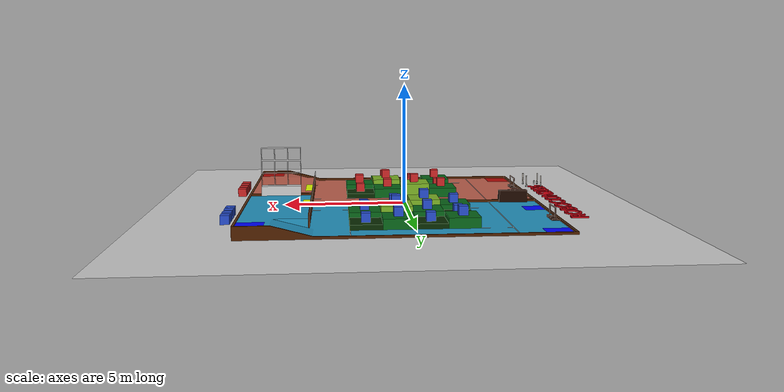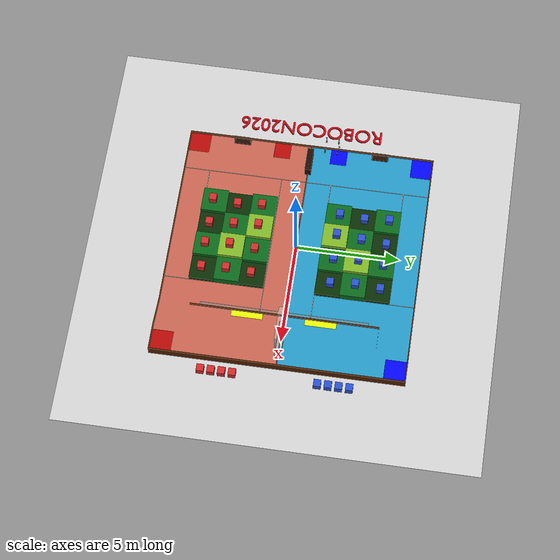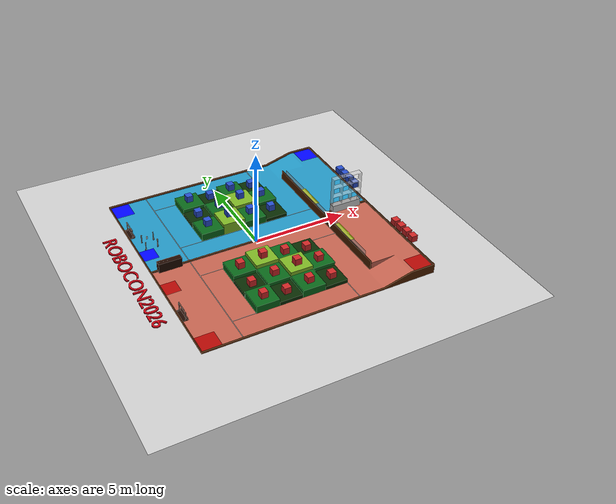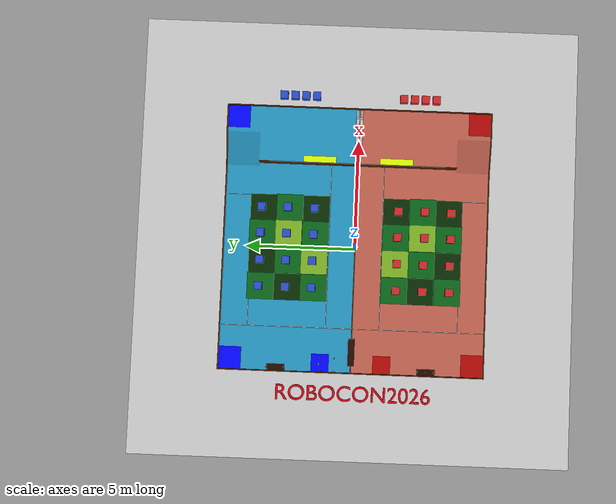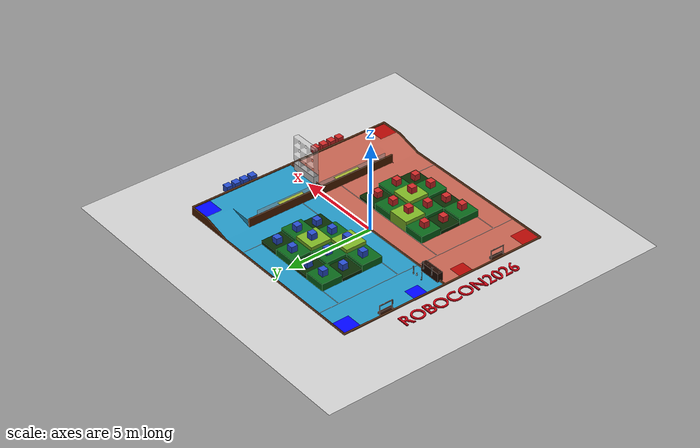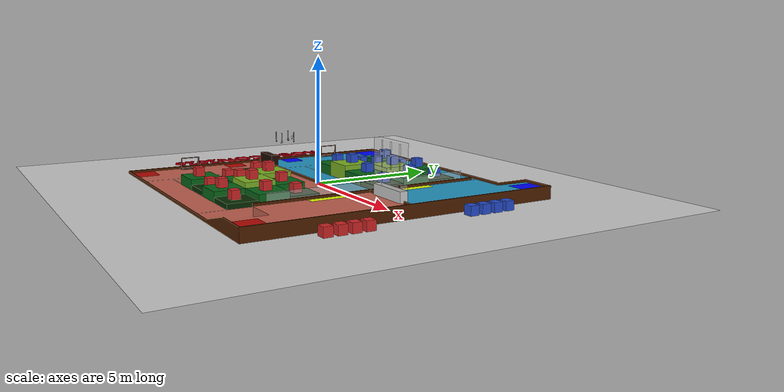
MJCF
<mujoco model="MuJoCo Model">
  <!-- Include the costume R2 robot -->
  <compiler angle="radian" meshdir="../meshes/" texturedir="../meshes/"/>

  <size nkey="2"/>

  <visual>
    <global azimuth="120" elevation="-20"/>
    <headlight ambient="0.3 0.3 0.3" diffuse="0.6 0.6 0.6" specular="0 0 0"/>
  </visual>

  <default>
    <site size="0.001 0.005 0.005" group="3"/>
    <default class="costume_R2">
      <joint armature="0.01" damping="0.5" frictionloss="0.1"/>
      <site size="0.005 0.005 0.005" group="0"/>
      <default class="visual">
        <geom type="mesh" contype="0" conaffinity="0" group="1"/>
      </default>
      <default class="collision">
        <geom type="mesh" group="3" friction="0.6" rgba="0.8 0.2 0.2 0.5"/>
      </default>
    </default>
    <default class="scene_attribute">
      <default class="scene_visual">
        <geom contype="0" conaffinity="0" group="2"/>
      </default>
      <default class="scene_collision">
        <geom type="mesh" conaffinity="0" group="3" priority="1" friction="0.6"/>
      </default>
    </default>
  </default>

  <asset>
    <texture type="skybox" colorspace="auto" builtin="gradient" rgb1="0.3 0.5 0.7" rgb2="0 0 0" width="512" height="3072"/>
    <texture type="2d" colorspace="auto" name="groundplane" builtin="checker" mark="edge" rgb1="0.2 0.3 0.4" rgb2="0.1 0.2 0.3" markrgb="0.8 0.8 0.8" width="300" height="300"/>
    <texture type="2d" colorspace="linear" name="kfs_R1_KFS_blue_texture" file="kfs/textures/blueR1KFS.png"/>
    <texture type="2d" colorspace="linear" name="kfs_R1_KFS_red_texture" file="kfs/textures/redR1KFS.png"/>
    <texture type="2d" colorspace="linear" name="kfs_redR001_texture" file="kfs/textures/red1.png"/>
    <texture type="2d" colorspace="linear" name="kfs_redR002_texture" file="kfs/textures/red2.png"/>
    <texture type="2d" colorspace="linear" name="kfs_redR003_texture" file="kfs/textures/red3.png"/>
    <texture type="2d" colorspace="linear" name="kfs_redR004_texture" file="kfs/textures/red4.png"/>
    <texture type="2d" colorspace="linear" name="kfs_redR005_texture" file="kfs/textures/red5.png"/>
    <texture type="2d" colorspace="linear" name="kfs_redR006_texture" file="kfs/textures/red6.png"/>
    <texture type="2d" colorspace="linear" name="kfs_redR007_texture" file="kfs/textures/red7.png"/>
    <texture type="2d" colorspace="linear" name="kfs_redR008_texture" file="kfs/textures/red8.png"/>
    <texture type="2d" colorspace="linear" name="kfs_redR009_texture" file="kfs/textures/red9.png"/>
    <texture type="2d" colorspace="linear" name="kfs_redR010_texture" file="kfs/textures/red10.png"/>
    <texture type="2d" colorspace="linear" name="kfs_redR011_texture" file="kfs/textures/red11.png"/>
    <texture type="2d" colorspace="linear" name="kfs_redR012_texture" file="kfs/textures/red12.png"/>
    <texture type="2d" colorspace="linear" name="kfs_redR013_texture" file="kfs/textures/red13.png"/>
    <texture type="2d" colorspace="linear" name="kfs_redR014_texture" file="kfs/textures/red14.png"/>
    <texture type="2d" colorspace="linear" name="kfs_redR015_texture" file="kfs/textures/red15.png"/>
    <texture type="2d" colorspace="linear" name="kfs_blueR001_texture" file="kfs/textures/blue1.png"/>
    <texture type="2d" colorspace="linear" name="kfs_blueR002_texture" file="kfs/textures/blue2.png"/>
    <texture type="2d" colorspace="linear" name="kfs_blueR003_texture" file="kfs/textures/blue3.png"/>
    <texture type="2d" colorspace="linear" name="kfs_blueR004_texture" file="kfs/textures/blue4.png"/>
    <texture type="2d" colorspace="linear" name="kfs_blueR005_texture" file="kfs/textures/blue5.png"/>
    <texture type="2d" colorspace="linear" name="kfs_blueR006_texture" file="kfs/textures/blue6.png"/>
    <texture type="2d" colorspace="linear" name="kfs_blueR007_texture" file="kfs/textures/blue7.png"/>
    <texture type="2d" colorspace="linear" name="kfs_blueR008_texture" file="kfs/textures/blue8.png"/>
    <texture type="2d" colorspace="linear" name="kfs_blueR009_texture" file="kfs/textures/blue9.png"/>
    <texture type="2d" colorspace="linear" name="kfs_blueR010_texture" file="kfs/textures/blue10.png"/>
    <texture type="2d" colorspace="linear" name="kfs_blueR011_texture" file="kfs/textures/blue11.png"/>
    <texture type="2d" colorspace="linear" name="kfs_blueR012_texture" file="kfs/textures/blue12.png"/>
    <texture type="2d" colorspace="linear" name="kfs_blueR013_texture" file="kfs/textures/blue13.png"/>
    <texture type="2d" colorspace="linear" name="kfs_blueR014_texture" file="kfs/textures/blue14.png"/>
    <texture type="2d" colorspace="linear" name="kfs_blueR015_texture" file="kfs/textures/blue15.png"/>
    <material name="base_material" rgba="0.898 0.918 0.929 1"/>
    <material name="rail_material" rgba="0.647 0.62 0.588 1"/>
    <material name="yaw_material" rgba="0.898 0.918 0.929 1"/>
    <material name="wheel_material" rgba="0.298 0.298 0.298 1"/>
    <material name="groundplane" texture="groundplane" texuniform="true" texrepeat="5 5" reflectance="0.2"/>
    <material name="robocon2026_blue_floor" shininess="0.25" rgba="0.136916 0.585362 0.758766 1"/>
    <material name="robocon2026_red_floor" shininess="0.25" rgba="0.756301 0.380415 0.306646 1"/>
    <material name="robocon2026_green" shininess="0.25" rgba="0.031974 0.394366 0.096107 1"/>
    <material name="robocon2026_mtl_009" shininess="0.25" rgba="0.8 0.012186 0.070887 1"/>
    <material name="robocon2026_mtl_9gg" shininess="0.25" rgba="0.8 0.8 0.8 1"/>
    <material name="robocon2026_mtl_floor" shininess="0.25" rgba="0.8 0.8 0.8 1"/>
    <material name="robocon2026_mtl_toumingge" shininess="0.81" rgba="0.8 0.8 0.8 0.5"/>
    <material name="robocon2026_sidebar" shininess="0.25" rgba="0.306829 0.122046 0 1"/>
    <material name="robocon2026_stair_green" shininess="0.25" rgba="0.034321 0.168246 0.010604 1"/>
    <material name="robocon2026_start_blue" shininess="0.25" rgba="0 0.013418 1 1"/>
    <material name="robocon2026_start_red" shininess="0.25" rgba="0.69903 0.029578 0.014299 1"/>
    <material name="robocon2026_weapon_grey" shininess="0.25" rgba="0.88379 1 0.001295 1"/>
    <material name="robocon2026_white_line" shininess="0.25" rgba="0.8 0.8 0.8 1"/>
    <material name="robocon2026_wood" shininess="0.250816" rgba="0.117286 0.033454 0 1"/>
    <material name="robocon2026_yellow" shininess="0.25" rgba="0.485941 0.697386 0.1426 1"/>
    <material name="kfs_R1_KFS_blue" texture="kfs_R1_KFS_blue_texture" shininess="0.341748"/>
    <material name="kfs_R1_KFS_red" texture="kfs_R1_KFS_red_texture" shininess="0.341748"/>
    <material name="kfs_redR001" texture="kfs_redR001_texture" shininess="0.341748"/>
    <material name="kfs_redR002" texture="kfs_redR002_texture" shininess="0.341748"/>
    <material name="kfs_redR003" texture="kfs_redR003_texture" shininess="0.341748"/>
    <material name="kfs_redR004" texture="kfs_redR004_texture" shininess="0.341748"/>
    <material name="kfs_redR005" texture="kfs_redR005_texture" shininess="0.341748"/>
    <material name="kfs_redR006" texture="kfs_redR006_texture" shininess="0.341748"/>
    <material name="kfs_redR007" texture="kfs_redR007_texture" shininess="0.341748"/>
    <material name="kfs_redR008" texture="kfs_redR008_texture" shininess="0.341748"/>
    <material name="kfs_redR009" texture="kfs_redR009_texture" shininess="0.341748"/>
    <material name="kfs_redR010" texture="kfs_redR010_texture" shininess="0.341748"/>
    <material name="kfs_redR011" texture="kfs_redR011_texture" shininess="0.341748"/>
    <material name="kfs_redR012" texture="kfs_redR012_texture" shininess="0.341748"/>
    <material name="kfs_redR013" texture="kfs_redR013_texture" shininess="0.341748"/>
    <material name="kfs_redR014" texture="kfs_redR014_texture" shininess="0.341748"/>
    <material name="kfs_redR015" texture="kfs_redR015_texture" shininess="0.341748"/>
    <material name="kfs_blueR001" texture="kfs_blueR001_texture" shininess="0.341748"/>
    <material name="kfs_blueR002" texture="kfs_blueR002_texture" shininess="0.341748"/>
    <material name="kfs_blueR003" texture="kfs_blueR003_texture" shininess="0.341748"/>
    <material name="kfs_blueR004" texture="kfs_blueR004_texture" shininess="0.341748"/>
    <material name="kfs_blueR005" texture="kfs_blueR005_texture" shininess="0.341748"/>
    <material name="kfs_blueR006" texture="kfs_blueR006_texture" shininess="0.341748"/>
    <material name="kfs_blueR007" texture="kfs_blueR007_texture" shininess="0.341748"/>
    <material name="kfs_blueR008" texture="kfs_blueR008_texture" shininess="0.341748"/>
    <material name="kfs_blueR009" texture="kfs_blueR009_texture" shininess="0.341748"/>
    <material name="kfs_blueR010" texture="kfs_blueR010_texture" shininess="0.341748"/>
    <material name="kfs_blueR011" texture="kfs_blueR011_texture" shininess="0.341748"/>
    <material name="kfs_blueR012" texture="kfs_blueR012_texture" shininess="0.341748"/>
    <material name="kfs_blueR013" texture="kfs_blueR013_texture" shininess="0.341748"/>
    <material name="kfs_blueR014" texture="kfs_blueR014_texture" shininess="0.341748"/>
    <material name="kfs_blueR015" texture="kfs_blueR015_texture" shininess="0.341748"/>
    <mesh name="base_link_vis" content_type="model/stl" file="/home/yxm/ROBOCON2026_Scene/models/robots/costume_R2/meshes/visual/base_link.STL"/>
    <mesh name="LF_rail_link_vis" content_type="model/stl" file="/home/yxm/ROBOCON2026_Scene/models/robots/costume_R2/meshes/visual/LF_rail_link.STL"/>
    <mesh name="LF_yaw_link_vis" content_type="model/stl" file="/home/yxm/ROBOCON2026_Scene/models/robots/costume_R2/meshes/visual/LF_yaw_link.STL"/>
    <mesh name="LF_wheel_link_vis" content_type="model/stl" file="/home/yxm/ROBOCON2026_Scene/models/robots/costume_R2/meshes/visual/LF_wheel_link.STL"/>
    <mesh name="LR_rail_link_vis" content_type="model/stl" file="/home/yxm/ROBOCON2026_Scene/models/robots/costume_R2/meshes/visual/LR_rail_link.STL"/>
    <mesh name="LR_yaw_link_vis" content_type="model/stl" file="/home/yxm/ROBOCON2026_Scene/models/robots/costume_R2/meshes/visual/LR_yaw_link.STL"/>
    <mesh name="LR_wheel_link_vis" content_type="model/stl" file="/home/yxm/ROBOCON2026_Scene/models/robots/costume_R2/meshes/visual/LR_wheel_link.STL"/>
    <mesh name="RF_rail_link_vis" content_type="model/stl" file="/home/yxm/ROBOCON2026_Scene/models/robots/costume_R2/meshes/visual/RF_rail_link.STL"/>
    <mesh name="RF_yaw_link_vis" content_type="model/stl" file="/home/yxm/ROBOCON2026_Scene/models/robots/costume_R2/meshes/visual/RF_yaw_link.STL"/>
    <mesh name="RF_wheel_link_vis" content_type="model/stl" file="/home/yxm/ROBOCON2026_Scene/models/robots/costume_R2/meshes/visual/RF_wheel_link.STL"/>
    <mesh name="RR_rail_link_vis" content_type="model/stl" file="/home/yxm/ROBOCON2026_Scene/models/robots/costume_R2/meshes/visual/RR_rail_link.STL"/>
    <mesh name="RR_yaw_link_vis" content_type="model/stl" file="/home/yxm/ROBOCON2026_Scene/models/robots/costume_R2/meshes/visual/RR_yaw_link.STL"/>
    <mesh name="RR_wheel_link_vis" content_type="model/stl" file="/home/yxm/ROBOCON2026_Scene/models/robots/costume_R2/meshes/visual/RR_wheel_link.STL"/>
    <mesh name="base_link_col" content_type="model/stl" file="/home/yxm/ROBOCON2026_Scene/models/robots/costume_R2/meshes/collision/base_link.STL"/>
    <mesh name="LF_rail_link_col" content_type="model/stl" file="/home/yxm/ROBOCON2026_Scene/models/robots/costume_R2/meshes/collision/LF_rail_link.STL"/>
    <mesh name="LF_yaw_link_col" content_type="model/stl" file="/home/yxm/ROBOCON2026_Scene/models/robots/costume_R2/meshes/collision/LF_yaw_link.STL"/>
    <mesh name="LR_rail_link_col" content_type="model/stl" file="/home/yxm/ROBOCON2026_Scene/models/robots/costume_R2/meshes/collision/LR_rail_link.STL"/>
    <mesh name="LR_yaw_link_col" content_type="model/stl" file="/home/yxm/ROBOCON2026_Scene/models/robots/costume_R2/meshes/collision/LR_yaw_link.STL"/>
    <mesh name="RF_rail_link_col" content_type="model/stl" file="/home/yxm/ROBOCON2026_Scene/models/robots/costume_R2/meshes/collision/RF_rail_link.STL"/>
    <mesh name="RF_yaw_link_col" content_type="model/stl" file="/home/yxm/ROBOCON2026_Scene/models/robots/costume_R2/meshes/collision/RF_yaw_link.STL"/>
    <mesh name="RR_rail_link_col" content_type="model/stl" file="/home/yxm/ROBOCON2026_Scene/models/robots/costume_R2/meshes/collision/RR_rail_link.STL"/>
    <mesh name="RR_yaw_link_col" content_type="model/stl" file="/home/yxm/ROBOCON2026_Scene/models/robots/costume_R2/meshes/collision/RR_yaw_link.STL"/>
    <mesh name="robocon2026_0" content_type="model/obj" file="visual/robocon2026_0.obj"/>
    <mesh name="robocon2026_2" content_type="model/obj" file="visual/robocon2026_2.obj"/>
    <mesh name="robocon2026_3" content_type="model/obj" file="visual/robocon2026_3.obj"/>
    <mesh name="robocon2026_4" content_type="model/obj" file="visual/robocon2026_4.obj"/>
    <mesh name="robocon2026_8" content_type="model/obj" file="visual/robocon2026_8.obj"/>
    <mesh name="robocon2026_9" content_type="model/obj" file="visual/robocon2026_9.obj"/>
    <mesh name="robocon2026_10" content_type="model/obj" file="visual/robocon2026_10.obj" inertia="shell"/>
    <mesh name="robocon2026_11" content_type="model/obj" file="visual/robocon2026_11.obj" inertia="shell"/>
    <mesh name="robocon2026_12" content_type="model/obj" file="visual/robocon2026_12.obj" inertia="shell"/>
    <mesh name="robocon2026_13" content_type="model/obj" file="visual/robocon2026_13.obj" inertia="shell"/>
    <mesh name="robocon2026_15" content_type="model/obj" file="visual/robocon2026_15.obj"/>
    <mesh name="robocon2026_16" content_type="model/obj" file="visual/robocon2026_16.obj"/>
    <mesh name="robocon2026_17" content_type="model/obj" file="visual/robocon2026_17.obj"/>
    <mesh name="robocon2026_18" content_type="model/obj" file="visual/robocon2026_18.obj" inertia="shell"/>
    <mesh name="robocon2026_19" content_type="model/obj" file="visual/robocon2026_19.obj"/>
    <mesh name="scene_part_001" content_type="model/obj" file="parts/part_001.obj"/>
    <mesh name="part_002_part_0" content_type="model/obj" file="parts/part_002/part_0.obj"/>
    <mesh name="part_002_part_1" content_type="model/obj" file="parts/part_002/part_1.obj"/>
    <mesh name="part_002_part_2" content_type="model/obj" file="parts/part_002/part_2.obj"/>
    <mesh name="part_002_part_3" content_type="model/obj" file="parts/part_002/part_3.obj"/>
    <mesh name="part_002_part_4" content_type="model/obj" file="parts/part_002/part_4.obj"/>
    <mesh name="part_002_part_5" content_type="model/obj" file="parts/part_002/part_5.obj"/>
    <mesh name="part_002_part_6" content_type="model/obj" file="parts/part_002/part_6.obj"/>
    <mesh name="part_002_part_7" content_type="model/obj" file="parts/part_002/part_7.obj"/>
    <mesh name="part_005_part_0" content_type="model/obj" file="parts/part_005/part_0.obj"/>
    <mesh name="part_005_part_1" content_type="model/obj" file="parts/part_005/part_1.obj"/>
    <mesh name="part_005_part_2" content_type="model/obj" file="parts/part_005/part_2.obj"/>
    <mesh name="part_005_part_3" content_type="model/obj" file="parts/part_005/part_3.obj"/>
    <mesh name="part_005_part_4" content_type="model/obj" file="parts/part_005/part_4.obj"/>
    <mesh name="part_005_part_5" content_type="model/obj" file="parts/part_005/part_5.obj"/>
    <mesh name="part_005_part_6" content_type="model/obj" file="parts/part_005/part_6.obj"/>
    <mesh name="part_010_part_0" content_type="model/obj" file="parts/part_010/part_0.obj"/>
    <mesh name="part_010_part_1" content_type="model/obj" file="parts/part_010/part_1.obj"/>
    <mesh name="part_010_part_2" content_type="model/obj" file="parts/part_010/part_2.obj"/>
    <mesh name="part_010_part_3" content_type="model/obj" file="parts/part_010/part_3.obj"/>
    <mesh name="part_010_part_4" content_type="model/obj" file="parts/part_010/part_4.obj"/>
    <mesh name="part_010_part_5" content_type="model/obj" file="parts/part_010/part_5.obj"/>
    <mesh name="part_010_part_6" content_type="model/obj" file="parts/part_010/part_6.obj"/>
    <mesh name="part_010_part_7" content_type="model/obj" file="parts/part_010/part_7.obj"/>
    <mesh name="part_010_part_8" content_type="model/obj" file="parts/part_010/part_8.obj"/>
    <mesh name="part_010_part_9" content_type="model/obj" file="parts/part_010/part_9.obj"/>
    <mesh name="part_010_part_10" content_type="model/obj" file="parts/part_010/part_10.obj"/>
    <mesh name="part_010_part_11" content_type="model/obj" file="parts/part_010/part_11.obj"/>
    <mesh name="part_010_part_12" content_type="model/obj" file="parts/part_010/part_12.obj"/>
    <mesh name="part_010_part_13" content_type="model/obj" file="parts/part_010/part_13.obj"/>
    <mesh name="part_010_part_14" content_type="model/obj" file="parts/part_010/part_14.obj"/>
    <mesh name="part_010_part_15" content_type="model/obj" file="parts/part_010/part_15.obj"/>
    <mesh name="part_010_part_16" content_type="model/obj" file="parts/part_010/part_16.obj"/>
    <mesh name="part_010_part_17" content_type="model/obj" file="parts/part_010/part_17.obj"/>
    <mesh name="part_010_part_18" content_type="model/obj" file="parts/part_010/part_18.obj"/>
    <mesh name="part_010_part_19" content_type="model/obj" file="parts/part_010/part_19.obj"/>
    <mesh name="part_010_part_20" content_type="model/obj" file="parts/part_010/part_20.obj"/>
    <mesh name="part_010_part_21" content_type="model/obj" file="parts/part_010/part_21.obj"/>
    <mesh name="part_010_part_22" content_type="model/obj" file="parts/part_010/part_22.obj"/>
    <mesh name="part_010_part_23" content_type="model/obj" file="parts/part_010/part_23.obj"/>
    <mesh name="part_011_part_0" content_type="model/obj" file="parts/part_011/part_0.obj"/>
    <mesh name="part_011_part_1" content_type="model/obj" file="parts/part_011/part_1.obj"/>
    <mesh name="part_011_part_2" content_type="model/obj" file="parts/part_011/part_2.obj"/>
    <mesh name="part_011_part_3" content_type="model/obj" file="parts/part_011/part_3.obj"/>
    <mesh name="part_011_part_4" content_type="model/obj" file="parts/part_011/part_4.obj"/>
    <mesh name="part_011_part_5" content_type="model/obj" file="parts/part_011/part_5.obj"/>
    <mesh name="part_011_part_6" content_type="model/obj" file="parts/part_011/part_6.obj"/>
    <mesh name="part_011_part_7" content_type="model/obj" file="parts/part_011/part_7.obj"/>
    <mesh name="part_011_part_8" content_type="model/obj" file="parts/part_011/part_8.obj"/>
    <mesh name="part_011_part_9" content_type="model/obj" file="parts/part_011/part_9.obj"/>
    <mesh name="part_011_part_10" content_type="model/obj" file="parts/part_011/part_10.obj"/>
    <mesh name="part_011_part_11" content_type="model/obj" file="parts/part_011/part_11.obj"/>
    <mesh name="part_011_part_12" content_type="model/obj" file="parts/part_011/part_12.obj"/>
    <mesh name="part_011_part_13" content_type="model/obj" file="parts/part_011/part_13.obj"/>
    <mesh name="part_011_part_14" content_type="model/obj" file="parts/part_011/part_14.obj"/>
    <mesh name="part_011_part_15" content_type="model/obj" file="parts/part_011/part_15.obj"/>
    <mesh name="part_011_part_16" content_type="model/obj" file="parts/part_011/part_16.obj"/>
    <mesh name="part_011_part_17" content_type="model/obj" file="parts/part_011/part_17.obj"/>
    <mesh name="part_011_part_18" content_type="model/obj" file="parts/part_011/part_18.obj"/>
    <mesh name="part_011_part_19" content_type="model/obj" file="parts/part_011/part_19.obj"/>
    <mesh name="part_011_part_20" content_type="model/obj" file="parts/part_011/part_20.obj"/>
    <mesh name="part_011_part_21" content_type="model/obj" file="parts/part_011/part_21.obj"/>
    <mesh name="part_011_part_22" content_type="model/obj" file="parts/part_011/part_22.obj"/>
    <mesh name="part_011_part_23" content_type="model/obj" file="parts/part_011/part_23.obj"/>
    <mesh name="part_011_part_24" content_type="model/obj" file="parts/part_011/part_24.obj"/>
    <mesh name="part_011_part_25" content_type="model/obj" file="parts/part_011/part_25.obj"/>
    <mesh name="scene_part_020" content_type="model/obj" file="parts/part_020.obj"/>
    <mesh name="scene_part_021" content_type="model/obj" file="parts/part_021.obj"/>
    <mesh name="scene_part_022" content_type="model/obj" file="parts/part_022.obj"/>
    <mesh name="scene_part_023" content_type="model/obj" file="parts/part_023.obj"/>
    <mesh name="scene_part_024" content_type="model/obj" file="parts/part_024.obj"/>
    <mesh name="scene_part_025" content_type="model/obj" file="parts/part_025.obj"/>
    <mesh name="scene_part_026" content_type="model/obj" file="parts/part_026.obj"/>
    <mesh name="scene_part_027" content_type="model/obj" file="parts/part_027.obj"/>
    <mesh name="scene_part_028" content_type="model/obj" file="parts/part_028.obj"/>
    <mesh name="scene_part_029" content_type="model/obj" file="parts/part_029.obj"/>
    <mesh name="scene_part_030" content_type="model/obj" file="parts/part_030.obj"/>
    <mesh name="scene_part_031" content_type="model/obj" file="parts/part_031.obj"/>
    <mesh name="scene_part_032" content_type="model/obj" file="parts/part_032.obj"/>
    <mesh name="scene_part_033" content_type="model/obj" file="parts/part_033.obj"/>
    <mesh name="scene_part_034" content_type="model/obj" file="parts/part_034.obj"/>
    <mesh name="scene_part_035" content_type="model/obj" file="parts/part_035.obj"/>
    <mesh name="scene_part_036" content_type="model/obj" file="parts/part_036.obj"/>
    <mesh name="scene_part_037" content_type="model/obj" file="parts/part_037.obj"/>
    <mesh name="scene_part_038" content_type="model/obj" file="parts/part_038.obj"/>
    <mesh name="scene_part_039" content_type="model/obj" file="parts/part_039.obj"/>
    <mesh name="scene_part_040" content_type="model/obj" file="parts/part_040.obj"/>
    <mesh name="scene_part_041" content_type="model/obj" file="parts/part_041.obj"/>
    <mesh name="scene_part_042" content_type="model/obj" file="parts/part_042.obj"/>
    <mesh name="scene_part_043" content_type="model/obj" file="parts/part_043.obj"/>
    <mesh name="part_044_part_0" content_type="model/obj" file="parts/part_044/part_0.obj"/>
    <mesh name="part_044_part_1" content_type="model/obj" file="parts/part_044/part_1.obj"/>
    <mesh name="part_044_part_2" content_type="model/obj" file="parts/part_044/part_2.obj"/>
    <mesh name="scene_part_045" content_type="model/obj" file="parts/part_045.obj"/>
    <mesh name="scene_part_046" content_type="model/obj" file="parts/part_046.obj"/>
    <mesh name="scene_part_047" content_type="model/obj" file="parts/part_047.obj"/>
    <mesh name="part_048_part_0" content_type="model/obj" file="parts/part_048/part_0.obj"/>
    <mesh name="part_048_part_1" content_type="model/obj" file="parts/part_048/part_1.obj"/>
    <mesh name="part_049_part_0" content_type="model/obj" file="parts/part_049/part_0.obj"/>
    <mesh name="part_049_part_1" content_type="model/obj" file="parts/part_049/part_1.obj"/>
    <mesh name="part_049_part_2" content_type="model/obj" file="parts/part_049/part_2.obj"/>
    <mesh name="scene_part_054" content_type="model/obj" file="parts/part_054.obj"/>
    <mesh name="scene_part_055" content_type="model/obj" file="parts/part_055.obj"/>
    <mesh name="parts_056_part_0" content_type="model/obj" file="parts/parts_056/part_0.obj"/>
    <mesh name="parts_056_part_1" content_type="model/obj" file="parts/parts_056/part_1.obj"/>
    <mesh name="parts_056_part_2" content_type="model/obj" file="parts/parts_056/part_2.obj"/>
    <mesh name="parts_056_part_3" content_type="model/obj" file="parts/parts_056/part_3.obj"/>
    <mesh name="parts_056_part_4" content_type="model/obj" file="parts/parts_056/part_4.obj"/>
    <mesh name="parts_056_part_5" content_type="model/obj" file="parts/parts_056/part_5.obj"/>
    <mesh name="parts_056_part_6" content_type="model/obj" file="parts/parts_056/part_6.obj"/>
    <mesh name="parts_056_part_7" content_type="model/obj" file="parts/parts_056/part_7.obj"/>
    <mesh name="parts_056_part_8" content_type="model/obj" file="parts/parts_056/part_8.obj"/>
    <mesh name="parts_056_part_9" content_type="model/obj" file="parts/parts_056/part_9.obj"/>
    <mesh name="parts_056_part_10" content_type="model/obj" file="parts/parts_056/part_10.obj"/>
    <mesh name="parts_056_part_11" content_type="model/obj" file="parts/parts_056/part_11.obj"/>
    <mesh name="parts_056_part_12" content_type="model/obj" file="parts/parts_056/part_12.obj"/>
    <mesh name="parts_056_part_13" content_type="model/obj" file="parts/parts_056/part_13.obj"/>
    <mesh name="parts_056_part_14" content_type="model/obj" file="parts/parts_056/part_14.obj"/>
    <mesh name="parts_056_part_15" content_type="model/obj" file="parts/parts_056/part_15.obj"/>
    <mesh name="parts_056_part_16" content_type="model/obj" file="parts/parts_056/part_16.obj"/>
    <mesh name="parts_056_part_17" content_type="model/obj" file="parts/parts_056/part_17.obj"/>
    <mesh name="parts_056_part_18" content_type="model/obj" file="parts/parts_056/part_18.obj"/>
    <mesh name="parts_056_part_19" content_type="model/obj" file="parts/parts_056/part_19.obj"/>
    <mesh name="parts_056_part_20" content_type="model/obj" file="parts/parts_056/part_20.obj"/>
    <mesh name="parts_056_part_21" content_type="model/obj" file="parts/parts_056/part_21.obj"/>
    <mesh name="parts_056_part_22" content_type="model/obj" file="parts/parts_056/part_22.obj"/>
    <mesh name="parts_056_part_23" content_type="model/obj" file="parts/parts_056/part_23.obj"/>
    <mesh name="parts_056_part_24" content_type="model/obj" file="parts/parts_056/part_24.obj"/>
    <mesh name="parts_056_part_25" content_type="model/obj" file="parts/parts_056/part_25.obj"/>
    <mesh name="parts_056_part_26" content_type="model/obj" file="parts/parts_056/part_26.obj"/>
    <mesh name="parts_056_part_27" content_type="model/obj" file="parts/parts_056/part_27.obj"/>
    <mesh name="parts_056_part_28" content_type="model/obj" file="parts/parts_056/part_28.obj"/>
    <mesh name="parts_056_part_29" content_type="model/obj" file="parts/parts_056/part_29.obj"/>
    <mesh name="parts_056_part_30" content_type="model/obj" file="parts/parts_056/part_30.obj"/>
    <mesh name="parts_056_part_31" content_type="model/obj" file="parts/parts_056/part_31.obj"/>
    <mesh name="parts_056_part_32" content_type="model/obj" file="parts/parts_056/part_32.obj"/>
    <mesh name="parts_056_part_33" content_type="model/obj" file="parts/parts_056/part_33.obj"/>
    <mesh name="parts_056_part_34" content_type="model/obj" file="parts/parts_056/part_34.obj"/>
    <mesh name="parts_056_part_35" content_type="model/obj" file="parts/parts_056/part_35.obj"/>
    <mesh name="parts_056_part_36" content_type="model/obj" file="parts/parts_056/part_36.obj"/>
    <mesh name="parts_056_part_37" content_type="model/obj" file="parts/parts_056/part_37.obj"/>
    <mesh name="parts_056_part_38" content_type="model/obj" file="parts/parts_056/part_38.obj"/>
    <mesh name="parts_056_part_39" content_type="model/obj" file="parts/parts_056/part_39.obj"/>
    <mesh name="parts_056_part_40" content_type="model/obj" file="parts/parts_056/part_40.obj"/>
    <mesh name="parts_056_part_41" content_type="model/obj" file="parts/parts_056/part_41.obj"/>
    <mesh name="parts_056_part_42" content_type="model/obj" file="parts/parts_056/part_42.obj"/>
    <mesh name="parts_056_part_43" content_type="model/obj" file="parts/parts_056/part_43.obj"/>
    <mesh name="parts_056_part_44" content_type="model/obj" file="parts/parts_056/part_44.obj"/>
    <mesh name="parts_056_part_45" content_type="model/obj" file="parts/parts_056/part_45.obj"/>
    <mesh name="parts_056_part_46" content_type="model/obj" file="parts/parts_056/part_46.obj"/>
    <mesh name="parts_056_part_47" content_type="model/obj" file="parts/parts_056/part_47.obj"/>
    <mesh name="parts_056_part_48" content_type="model/obj" file="parts/parts_056/part_48.obj"/>
    <mesh name="parts_056_part_49" content_type="model/obj" file="parts/parts_056/part_49.obj"/>
    <mesh name="kfs_00" content_type="model/obj" file="kfs/kfs_00.obj"/>
    <mesh name="kfs_01" content_type="model/obj" file="kfs/kfs_01.obj"/>
    <mesh name="kfs_03" content_type="model/obj" file="kfs/kfs_03.obj"/>
    <mesh name="kfs_04" content_type="model/obj" file="kfs/kfs_04.obj"/>
    <mesh name="kfs_05" content_type="model/obj" file="kfs/kfs_05.obj"/>
    <mesh name="kfs_06" content_type="model/obj" file="kfs/kfs_06.obj"/>
    <mesh name="kfs_07" content_type="model/obj" file="kfs/kfs_07.obj"/>
    <mesh name="kfs_08" content_type="model/obj" file="kfs/kfs_08.obj"/>
    <mesh name="kfs_09" content_type="model/obj" file="kfs/kfs_09.obj"/>
    <mesh name="kfs_10" content_type="model/obj" file="kfs/kfs_10.obj"/>
    <mesh name="kfs_11" content_type="model/obj" file="kfs/kfs_11.obj"/>
    <mesh name="kfs_12" content_type="model/obj" file="kfs/kfs_12.obj"/>
    <mesh name="kfs_13" content_type="model/obj" file="kfs/kfs_13.obj"/>
    <mesh name="kfs_14" content_type="model/obj" file="kfs/kfs_14.obj"/>
    <mesh name="kfs_15" content_type="model/obj" file="kfs/kfs_15.obj"/>
    <mesh name="kfs_16" content_type="model/obj" file="kfs/kfs_16.obj"/>
    <mesh name="kfs_17" content_type="model/obj" file="kfs/kfs_17.obj"/>
    <mesh name="kfs_18" content_type="model/obj" file="kfs/kfs_18.obj"/>
    <mesh name="kfs_19" content_type="model/obj" file="kfs/kfs_19.obj"/>
    <mesh name="kfs_20" content_type="model/obj" file="kfs/kfs_20.obj"/>
    <mesh name="kfs_21" content_type="model/obj" file="kfs/kfs_21.obj"/>
    <mesh name="kfs_22" content_type="model/obj" file="kfs/kfs_22.obj"/>
    <mesh name="kfs_23" content_type="model/obj" file="kfs/kfs_23.obj"/>
    <mesh name="kfs_24" content_type="model/obj" file="kfs/kfs_24.obj"/>
    <mesh name="kfs_25" content_type="model/obj" file="kfs/kfs_25.obj"/>
    <mesh name="kfs_26" content_type="model/obj" file="kfs/kfs_26.obj"/>
    <mesh name="kfs_27" content_type="model/obj" file="kfs/kfs_27.obj"/>
    <mesh name="kfs_28" content_type="model/obj" file="kfs/kfs_28.obj"/>
    <mesh name="kfs_29" content_type="model/obj" file="kfs/kfs_29.obj"/>
    <mesh name="kfs_30" content_type="model/obj" file="kfs/kfs_30.obj"/>
    <mesh name="kfs_31" content_type="model/obj" file="kfs/kfs_31.obj"/>
    <mesh name="kfs_32" content_type="model/obj" file="kfs/kfs_32.obj"/>
  </asset>

  <worldbody>
    <camera name="family_photo" pos="-8.583 -0.064 1.71" quat="0.618186 0.335926 -0.339302 -0.624399" fovy="75"/>
    <camera name="top_view" pos="0 0 20" quat="0.707107 0 0 -0.707107"/>
    <light pos="6 0 10" dir="0 0 -1"/>
    <light pos="-6 0 10" dir="0 0 -1"/>
    <light pos="0 6 10" dir="0 0 -1"/>
    <light pos="0 -6 10" dir="0 0 -1"/>
    <body name="base_link" childclass="costume_R2" pos="-5.2 1.4 1">
      <inertial pos="0.001206 -0.353411 0.016987" mass="2.80469" diaginertia="0.015653 0.013749 0.027267"/>
      <joint type="free" armature="0" damping="0" frictionloss="0"/>
      <geom name="base_geom_visual" class="visual" material="base_material" mesh="base_link_vis"/>
      <geom name="base_geom_collision" class="collision" mesh="base_link_col"/>
      <site name="imu_site" pos="0 0 0" size="0.01" rgba="1 0 0 1"/>
      <body name="LF_rail_link" pos="0.30193 -0.654 0.33384">
        <inertial pos="0.000323 0.001222 -0.193011" mass="0.423892" diaginertia="0.002686 0.002689 6.3e-05"/>
        <joint name="LF_rail_joint" pos="0 0 0" axis="0 0 -1" type="slide" limited="true" range="0 0.25" damping="10"/>
        <geom name="LF_rail_geom_visual" class="visual" material="rail_material" mesh="LF_rail_link_vis"/>
        <geom name="LF_rail_geom_collision" class="collision" mesh="LF_rail_link_col"/>
        <body name="LF_yaw_link" pos="0 0 -0.3778">
          <inertial pos="0.000568 0.00063 -0.032724" mass="0.077001" diaginertia="2.5e-05 2.5e-05 1.7e-05"/>
          <joint name="LF_yaw_joint" pos="0 0 0" axis="0 0 1" limited="true" range="-3.14 3.14" armature="0.001" damping="0.1"/>
          <geom name="LF_yaw_geom_visual" class="visual" material="yaw_material" mesh="LF_yaw_link_vis"/>
          <geom name="LF_yaw_geom_collision" class="collision" mesh="LF_yaw_link_col"/>
          <body name="LF_wheel_link" pos="-0.0098995 -0.0098995 -0.0465" quat="0.707107 0 0 -0.707107">
            <inertial pos="0 0 -0.010192" mass="0.057721" diaginertia="2.6e-05 2.6e-05 4.3e-05"/>
            <joint name="LF_wheel_joint" pos="0 0 0" axis="0 0 -1" armature="0.001" damping="0.05"/>
            <geom name="LF_wheel_geom_visual" class="visual" material="wheel_material" mesh="LF_wheel_link_vis"/>
            <geom name="LF_wheel_geom_collision" class="collision" size="0.05" type="sphere"/>
          </body>
        </body>
      </body>
      <body name="LR_rail_link" pos="0.30193 -0.054 0.33384">
        <inertial pos="-0.000289 0.001114 -0.191038" mass="0.466755" diaginertia="0.003109 0.003112 6.8e-05"/>
        <joint name="LR_rail_joint" pos="0 0 0" axis="0 0 -1" type="slide" limited="true" range="0 0.25" damping="10"/>
        <geom name="LR_rail_geom_visual" class="visual" material="rail_material" mesh="LR_rail_link_vis"/>
        <geom name="LR_rail_geom_collision" class="collision" mesh="LR_rail_link_col"/>
        <body name="LR_yaw_link" pos="0 0 -0.3778">
          <inertial pos="-0.00063 0.000568 -0.032724" mass="0.077001" diaginertia="2.5e-05 2.5e-05 1.7e-05"/>
          <joint name="LR_yaw_joint" pos="0 0 0" axis="0 0 1" limited="true" range="-3.14 3.14" armature="0.001" damping="0.1"/>
          <geom name="LR_yaw_geom_visual" class="visual" material="yaw_material" mesh="LR_yaw_link_vis"/>
          <geom name="LR_yaw_geom_collision" class="collision" mesh="LR_yaw_link_col"/>
          <body name="LR_wheel_link" pos="0.0098995 -0.0098995 -0.0465" quat="0.707107 0 0 0.707107">
            <inertial pos="0 0 -0.010192" mass="0.057721" diaginertia="2.6e-05 2.6e-05 4.3e-05"/>
            <joint name="LR_wheel_joint" pos="0 0 0" axis="0 0 -1" armature="0.001" damping="0.05"/>
            <geom name="LR_wheel_geom_visual" class="visual" material="wheel_material" mesh="LR_wheel_link_vis"/>
            <geom name="LR_wheel_geom_collision" class="collision" size="0.05" type="sphere"/>
          </body>
        </body>
      </body>
      <body name="RF_rail_link" pos="-0.29807 -0.654 0.33384">
        <inertial pos="0.000289 -0.001114 -0.191038" mass="0.466755" diaginertia="0.003109 0.003112 6.8e-05"/>
        <joint name="RF_rail_joint" pos="0 0 0" axis="0 0 -1" type="slide" limited="true" range="0 0.25" damping="10"/>
        <geom name="RF_rail_geom_visual" class="visual" material="rail_material" mesh="RF_rail_link_vis"/>
        <geom name="RF_rail_geom_collision" class="collision" mesh="RF_rail_link_col"/>
        <body name="RF_yaw_link" pos="0 0 -0.3778">
          <inertial pos="0.00063 -0.000568 -0.032724" mass="0.077001" diaginertia="2.5e-05 2.5e-05 1.7e-05"/>
          <joint name="RF_yaw_joint" pos="0 0 0" axis="0 0 1" limited="true" range="-3.14 3.14" armature="0.001" damping="0.1"/>
          <geom name="RF_yaw_geom_visual" class="visual" material="yaw_material" mesh="RF_yaw_link_vis"/>
          <geom name="RF_yaw_geom_collision" class="collision" mesh="RF_yaw_link_col"/>
          <body name="RF_wheel_link" pos="-0.0098995 0.0098995 -0.0465" quat="0.707107 0 0 -0.707107">
            <inertial pos="0 0 -0.010192" mass="0.057721" diaginertia="2.6e-05 2.6e-05 4.3e-05"/>
            <joint name="RF_wheel_joint" pos="0 0 0" axis="0 0 -1" armature="0.001" damping="0.05"/>
            <geom name="RF_wheel_geom_visual" class="visual" material="wheel_material" mesh="RF_wheel_link_vis"/>
            <geom name="RF_wheel_geom_collision" class="collision" size="0.05" type="sphere"/>
          </body>
        </body>
      </body>
      <body name="RR_rail_link" pos="-0.29807 -0.054 0.33384">
        <inertial pos="-0.000205 -0.000712 -0.191038" mass="0.466755" diaginertia="0.003109 0.003112 6.8e-05"/>
        <joint name="RR_rail_joint" pos="0 0 0" axis="0 0 -1" type="slide" limited="true" range="0 0.25" damping="10"/>
        <geom name="RR_rail_geom_visual" class="visual" material="rail_material" mesh="RR_rail_link_vis"/>
        <geom name="RR_rail_geom_collision" class="collision" mesh="RR_rail_link_col"/>
        <body name="RR_yaw_link" pos="0 0 -0.3778">
          <inertial pos="-0.000568 -0.00063 -0.032724" mass="0.077001" diaginertia="2.5e-05 2.5e-05 1.7e-05"/>
          <joint name="RR_yaw_joint" pos="0 0 0" axis="0 0 1" limited="true" range="-3.14 3.14" armature="0.001" damping="0.1"/>
          <geom name="RR_yaw_geom_visual" class="visual" material="yaw_material" mesh="RR_yaw_link_vis"/>
          <geom name="RR_yaw_geom_collision" class="collision" mesh="RR_yaw_link_col"/>
          <body name="RR_wheel_link" pos="0.0098995 0.0098995 -0.0465" quat="0.707107 0 0 0.707107">
            <inertial pos="0 0 -0.010192" mass="0.057721" diaginertia="2.6e-05 2.6e-05 4.3e-05"/>
            <joint name="RR_wheel_joint" pos="0 0 0" axis="0 0 -1" armature="0.001" damping="0.05"/>
            <geom name="RR_wheel_geom_visual" class="visual" material="wheel_material" mesh="RR_wheel_link_vis"/>
            <geom name="RR_wheel_geom_collision" class="collision" size="0.05" type="sphere"/>
          </body>
        </body>
      </body>
    </body>
    <body name="kfs_red_R1_00" pos="1.8 -1.9 0.38">
      <inertial pos="0 0 0" mass="0.01" diaginertia="0.002 0.002 0.002"/>
      <joint type="free" damping="0.0001"/>
      <geom class="scene_collision" conaffinity="1" group="1" material="kfs_R1_KFS_red" mesh="kfs_01"/>
    </body>
    <body name="kfs_red_01" pos="-0.6 -1.9 0.78">
      <inertial pos="0 0 0" mass="0.01" diaginertia="0.002 0.002 0.002"/>
      <joint type="free" damping="0.0001"/>
      <geom class="scene_collision" conaffinity="1" group="1" material="kfs_redR015" mesh="kfs_03"/>
    </body>
    <body name="kfs_red_02" pos="-1.8 -1.9 0.58">
      <inertial pos="0 0 0" mass="0.01" diaginertia="0.002 0.002 0.002"/>
      <joint type="free" damping="0.0001"/>
      <geom class="scene_collision" conaffinity="1" group="1" material="kfs_redR014" mesh="kfs_04"/>
    </body>
    <body name="kfs_red_03" pos="0.6 -3.1 0.78">
      <inertial pos="0 0 0" mass="0.01" diaginertia="0.002 0.002 0.002"/>
      <joint type="free" damping="0.0001"/>
      <geom class="scene_collision" conaffinity="1" group="1" material="kfs_redR013" mesh="kfs_05"/>
    </body>
    <body name="kfs_red_04" pos="1.8 -3.1 0.58">
      <inertial pos="0 0 0" mass="0.01" diaginertia="0.002 0.002 0.002"/>
      <joint type="free" damping="0.0001"/>
      <geom class="scene_collision" conaffinity="1" group="1" material="kfs_redR012" mesh="kfs_06"/>
    </body>
    <body name="kfs_red_05" pos="-0.6 -3.1 0.58">
      <inertial pos="0 0 0" mass="0.01" diaginertia="0.002 0.002 0.002"/>
      <joint type="free" damping="0.0001"/>
      <geom class="scene_collision" conaffinity="1" group="1" material="kfs_redR011" mesh="kfs_07"/>
    </body>
    <body name="kfs_red_06" pos="-1.8 -3.1 0.38">
      <inertial pos="0 0 0" mass="0.01" diaginertia="0.002 0.002 0.002"/>
      <joint type="free" damping="0.0001"/>
      <geom class="scene_collision" conaffinity="1" group="1" material="kfs_redR010" mesh="kfs_08"/>
    </body>
    <body name="kfs_red_07" pos="1.8 -4.3 0.38">
      <inertial pos="0 0 0" mass="0.01" diaginertia="0.002 0.002 0.002"/>
      <joint type="free" damping="0.0001"/>
      <geom class="scene_collision" conaffinity="1" group="1" material="kfs_redR009" mesh="kfs_09"/>
    </body>
    <body name="kfs_red_08" pos="0.6 -1.9 0.58">
      <inertial pos="0 0 0" mass="0.01" diaginertia="0.002 0.002 0.002"/>
      <joint type="free" damping="0.0001"/>
      <geom class="scene_collision" conaffinity="1" group="1" material="kfs_redR008" mesh="kfs_10"/>
    </body>
    <body name="kfs_red_09" pos="0.6 -4.3 0.58">
      <inertial pos="0 0 0" mass="0.01" diaginertia="0.002 0.002 0.002"/>
      <joint type="free" damping="0.0001"/>
      <geom class="scene_collision" conaffinity="1" group="1" material="kfs_redR007" mesh="kfs_11"/>
    </body>
    <body name="kfs_red_10" pos="-0.6 -4.3 0.38">
      <inertial pos="0 0 0" mass="0.01" diaginertia="0.002 0.002 0.002"/>
      <joint type="free" damping="0.0001"/>
      <geom class="scene_collision" conaffinity="1" group="1" material="kfs_redR006" mesh="kfs_12"/>
    </body>
    <body name="kfs_red_11" pos="-1.8 -4.3 0.58">
      <inertial pos="0 0 0" mass="0.01" diaginertia="0.002 0.002 0.002"/>
      <joint type="free" damping="0.0001"/>
      <geom class="scene_collision" conaffinity="1" group="1" material="kfs_redR005" mesh="kfs_13"/>
    </body>
    <body name="kfs_red_12" pos="7 -2 0.2">
      <inertial pos="0 0 0" mass="0.01" diaginertia="0.002 0.002 0.002"/>
      <joint type="free" damping="0.0001"/>
      <geom class="scene_collision" conaffinity="1" group="1" material="kfs_redR004" mesh="kfs_14"/>
    </body>
    <body name="kfs_red_13" pos="7 -2.5 0.2">
      <inertial pos="0 0 0" mass="0.01" diaginertia="0.002 0.002 0.002"/>
      <joint type="free" damping="0.0001"/>
      <geom class="scene_collision" conaffinity="1" group="1" material="kfs_redR003" mesh="kfs_15"/>
    </body>
    <body name="kfs_red_14" pos="7 -3 0.2">
      <inertial pos="0 0 0" mass="0.01" diaginertia="0.002 0.002 0.002"/>
      <joint type="free" damping="0.0001"/>
      <geom class="scene_collision" conaffinity="1" group="1" material="kfs_redR002" mesh="kfs_16"/>
    </body>
    <body name="kfs_red_15" pos="7 -3.5 0.2">
      <inertial pos="0 0 0" mass="0.01" diaginertia="0.002 0.002 0.002"/>
      <joint type="free" damping="0.0001"/>
      <geom class="scene_collision" conaffinity="1" group="1" material="kfs_redR001" mesh="kfs_17"/>
    </body>
    <body name="kfs_blue_R1_00" pos="1.8 1.9 0.38">
      <inertial pos="0 0 0" mass="0.01" diaginertia="0.002 0.002 0.002"/>
      <joint type="free" damping="0.0001"/>
      <geom class="scene_collision" conaffinity="1" group="1" material="kfs_R1_KFS_blue" mesh="kfs_00"/>
    </body>
    <body name="kfs_blue_01" pos="0.6 1.9 0.58">
      <inertial pos="0 0 0" mass="0.01" diaginertia="0.002 0.002 0.002"/>
      <joint type="free" damping="0.0001"/>
      <geom class="scene_collision" conaffinity="1" group="1" material="kfs_blueR015" mesh="kfs_18"/>
    </body>
    <body name="kfs_blue_02" pos="-0.6 1.9 0.78">
      <inertial pos="0 0 0" mass="0.01" diaginertia="0.002 0.002 0.002"/>
      <joint type="free" damping="0.0001"/>
      <geom class="scene_collision" conaffinity="1" group="1" material="kfs_blueR014" mesh="kfs_19"/>
    </body>
    <body name="kfs_blue_03" pos="-1.8 1.9 0.58">
      <inertial pos="0 0 0" mass="0.01" diaginertia="0.002 0.002 0.002"/>
      <joint type="free" damping="0.0001"/>
      <geom class="scene_collision" conaffinity="1" group="1" material="kfs_blueR013" mesh="kfs_20"/>
    </body>
    <body name="kfs_blue_04" pos="0.6 3.1 0.78">
      <inertial pos="0 0 0" mass="0.01" diaginertia="0.002 0.002 0.002"/>
      <joint type="free" damping="0.0001"/>
      <geom class="scene_collision" conaffinity="1" group="1" material="kfs_blueR012" mesh="kfs_21"/>
    </body>
    <body name="kfs_blue_05" pos="1.8 3.1 0.58">
      <inertial pos="0 0 0" mass="0.01" diaginertia="0.002 0.002 0.002"/>
      <joint type="free" damping="0.0001"/>
      <geom class="scene_collision" conaffinity="1" group="1" material="kfs_blueR011" mesh="kfs_22"/>
    </body>
    <body name="kfs_blue_06" pos="-0.6 3.1 0.58">
      <inertial pos="0 0 0" mass="0.01" diaginertia="0.002 0.002 0.002"/>
      <joint type="free" damping="0.0001"/>
      <geom class="scene_collision" conaffinity="1" group="1" material="kfs_blueR010" mesh="kfs_23"/>
    </body>
    <body name="kfs_blue_07" pos="-1.8 3.1 0.38">
      <inertial pos="0 0 0" mass="0.01" diaginertia="0.002 0.002 0.002"/>
      <joint type="free" damping="0.0001"/>
      <geom class="scene_collision" conaffinity="1" group="1" material="kfs_blueR009" mesh="kfs_24"/>
    </body>
    <body name="kfs_blue_08" pos="1.8 4.3 0.38">
      <inertial pos="0 0 0" mass="0.01" diaginertia="0.002 0.002 0.002"/>
      <joint type="free" damping="0.0001"/>
      <geom class="scene_collision" conaffinity="1" group="1" material="kfs_blueR008" mesh="kfs_25"/>
    </body>
    <body name="kfs_blue_09" pos="0.6 4.3 0.58">
      <inertial pos="0 0 0" mass="0.01" diaginertia="0.002 0.002 0.002"/>
      <joint type="free" damping="0.0001"/>
      <geom class="scene_collision" conaffinity="1" group="1" material="kfs_blueR007" mesh="kfs_26"/>
    </body>
    <body name="kfs_blue_10" pos="-0.6 4.3 0.38">
      <inertial pos="0 0 0" mass="0.01" diaginertia="0.002 0.002 0.002"/>
      <joint type="free" damping="0.0001"/>
      <geom class="scene_collision" conaffinity="1" group="1" material="kfs_blueR006" mesh="kfs_27"/>
    </body>
    <body name="kfs_blue_11" pos="-1.8 4.3 0.58">
      <inertial pos="0 0 0" mass="0.01" diaginertia="0.002 0.002 0.002"/>
      <joint type="free" damping="0.0001"/>
      <geom class="scene_collision" conaffinity="1" group="1" material="kfs_blueR005" mesh="kfs_28"/>
    </body>
    <body name="kfs_blue_12" pos="7 2 0.2">
      <inertial pos="0 0 0" mass="0.01" diaginertia="0.002 0.002 0.002"/>
      <joint type="free" damping="0.0001"/>
      <geom class="scene_collision" conaffinity="1" group="1" material="kfs_blueR004" mesh="kfs_29"/>
    </body>
    <body name="kfs_blue_13" pos="7 2.5 0.2">
      <inertial pos="0 0 0" mass="0.01" diaginertia="0.002 0.002 0.002"/>
      <joint type="free" damping="0.0001"/>
      <geom class="scene_collision" conaffinity="1" group="1" material="kfs_blueR003" mesh="kfs_30"/>
    </body>
    <body name="kfs_blue_14" pos="7 3 0.2">
      <inertial pos="0 0 0" mass="0.01" diaginertia="0.002 0.002 0.002"/>
      <joint type="free" damping="0.0001"/>
      <geom class="scene_collision" conaffinity="1" group="1" material="kfs_blueR002" mesh="kfs_31"/>
    </body>
    <body name="kfs_blue_15" pos="7 3.5 0.2">
      <inertial pos="0 0 0" mass="0.01" diaginertia="0.002 0.002 0.002"/>
      <joint type="free" damping="0.0001"/>
      <geom class="scene_collision" conaffinity="1" group="1" material="kfs_blueR001" mesh="kfs_32"/>
    </body>
    <body name="scene" childclass="scene_attribute" pos="0.4 0 0">
      <body name="scene_visual">
        <geom class="scene_visual" type="mesh" material="robocon2026_mtl_9gg" mesh="robocon2026_0"/>
        <geom class="scene_visual" type="mesh" material="robocon2026_green" mesh="robocon2026_2"/>
        <geom class="scene_visual" type="mesh" material="robocon2026_stair_green" mesh="robocon2026_3"/>
        <geom class="scene_visual" type="mesh" material="robocon2026_yellow" mesh="robocon2026_4"/>
        <geom class="scene_visual" type="mesh" material="robocon2026_mtl_toumingge" mesh="robocon2026_8"/>
        <geom class="scene_visual" type="mesh" material="robocon2026_start_red" mesh="robocon2026_9"/>
        <geom class="scene_visual" type="mesh" material="robocon2026_weapon_grey" mesh="robocon2026_10"/>
        <geom class="scene_visual" type="mesh" material="robocon2026_white_line" mesh="robocon2026_11"/>
        <geom class="scene_visual" type="mesh" material="robocon2026_blue_floor" mesh="robocon2026_12"/>
        <geom class="scene_visual" type="mesh" material="robocon2026_red_floor" mesh="robocon2026_13"/>
        <geom class="scene_visual" type="mesh" material="robocon2026_start_blue" mesh="robocon2026_15"/>
        <geom class="scene_visual" type="mesh" material="robocon2026_wood" mesh="robocon2026_16"/>
        <geom class="scene_visual" type="mesh" material="robocon2026_sidebar" mesh="robocon2026_17"/>
        <geom class="scene_visual" type="mesh" material="robocon2026_mtl_floor" mesh="robocon2026_18"/>
        <geom class="scene_visual" type="mesh" material="robocon2026_mtl_009" mesh="robocon2026_19"/>
      </body>
      <body name="scene_collision">
        <geom name="floor" size="10 10 0.01" type="plane" group="3"/>
        <geom class="scene_collision" mesh="scene_part_001"/>
        <geom class="scene_collision" mesh="part_002_part_0"/>
        <geom class="scene_collision" mesh="part_002_part_1"/>
        <geom class="scene_collision" mesh="part_002_part_2"/>
        <geom class="scene_collision" mesh="part_002_part_3"/>
        <geom class="scene_collision" mesh="part_002_part_4"/>
        <geom class="scene_collision" mesh="part_002_part_5"/>
        <geom class="scene_collision" mesh="part_002_part_6"/>
        <geom class="scene_collision" mesh="part_002_part_7"/>
        <geom class="scene_collision" mesh="part_002_part_0"/>
        <geom class="scene_collision" mesh="part_002_part_1"/>
        <geom class="scene_collision" mesh="part_002_part_2"/>
        <geom class="scene_collision" mesh="part_002_part_3"/>
        <geom class="scene_collision" mesh="part_002_part_4"/>
        <geom class="scene_collision" mesh="part_002_part_5"/>
        <geom class="scene_collision" mesh="part_002_part_6"/>
        <geom class="scene_collision" mesh="part_002_part_7"/>
        <geom class="scene_collision" mesh="part_005_part_0"/>
        <geom class="scene_collision" mesh="part_005_part_1"/>
        <geom class="scene_collision" mesh="part_005_part_2"/>
        <geom class="scene_collision" mesh="part_005_part_3"/>
        <geom class="scene_collision" mesh="part_005_part_4"/>
        <geom class="scene_collision" mesh="part_005_part_5"/>
        <geom class="scene_collision" mesh="part_005_part_6"/>
        <geom class="scene_collision" mesh="part_010_part_0"/>
        <geom class="scene_collision" mesh="part_010_part_1"/>
        <geom class="scene_collision" mesh="part_010_part_2"/>
        <geom class="scene_collision" mesh="part_010_part_3"/>
        <geom class="scene_collision" mesh="part_010_part_4"/>
        <geom class="scene_collision" mesh="part_010_part_5"/>
        <geom class="scene_collision" mesh="part_010_part_6"/>
        <geom class="scene_collision" mesh="part_010_part_7"/>
        <geom class="scene_collision" mesh="part_010_part_8"/>
        <geom class="scene_collision" mesh="part_010_part_9"/>
        <geom class="scene_collision" mesh="part_010_part_10"/>
        <geom class="scene_collision" mesh="part_010_part_11"/>
        <geom class="scene_collision" mesh="part_010_part_12"/>
        <geom class="scene_collision" mesh="part_010_part_13"/>
        <geom class="scene_collision" mesh="part_010_part_14"/>
        <geom class="scene_collision" mesh="part_010_part_15"/>
        <geom class="scene_collision" mesh="part_010_part_16"/>
        <geom class="scene_collision" mesh="part_010_part_17"/>
        <geom class="scene_collision" mesh="part_010_part_18"/>
        <geom class="scene_collision" mesh="part_010_part_19"/>
        <geom class="scene_collision" mesh="part_010_part_20"/>
        <geom class="scene_collision" mesh="part_010_part_21"/>
        <geom class="scene_collision" mesh="part_010_part_22"/>
        <geom class="scene_collision" mesh="part_010_part_23"/>
        <geom class="scene_collision" mesh="part_011_part_0"/>
        <geom class="scene_collision" mesh="part_011_part_1"/>
        <geom class="scene_collision" mesh="part_011_part_2"/>
        <geom class="scene_collision" mesh="part_011_part_3"/>
        <geom class="scene_collision" mesh="part_011_part_4"/>
        <geom class="scene_collision" mesh="part_011_part_5"/>
        <geom class="scene_collision" mesh="part_011_part_6"/>
        <geom class="scene_collision" mesh="part_011_part_7"/>
        <geom class="scene_collision" mesh="part_011_part_8"/>
        <geom class="scene_collision" mesh="part_011_part_9"/>
        <geom class="scene_collision" mesh="part_011_part_10"/>
        <geom class="scene_collision" mesh="part_011_part_11"/>
        <geom class="scene_collision" mesh="part_011_part_12"/>
        <geom class="scene_collision" mesh="part_011_part_13"/>
        <geom class="scene_collision" mesh="part_011_part_14"/>
        <geom class="scene_collision" mesh="part_011_part_15"/>
        <geom class="scene_collision" mesh="part_011_part_16"/>
        <geom class="scene_collision" mesh="part_011_part_17"/>
        <geom class="scene_collision" mesh="part_011_part_18"/>
        <geom class="scene_collision" mesh="part_011_part_19"/>
        <geom class="scene_collision" mesh="part_011_part_20"/>
        <geom class="scene_collision" mesh="part_011_part_21"/>
        <geom class="scene_collision" mesh="part_011_part_22"/>
        <geom class="scene_collision" mesh="part_011_part_23"/>
        <geom class="scene_collision" mesh="part_011_part_24"/>
        <geom class="scene_collision" mesh="part_011_part_25"/>
        <geom class="scene_collision" mesh="scene_part_020"/>
        <geom class="scene_collision" mesh="scene_part_021"/>
        <geom class="scene_collision" mesh="scene_part_022"/>
        <geom class="scene_collision" mesh="scene_part_023"/>
        <geom class="scene_collision" mesh="scene_part_024"/>
        <geom class="scene_collision" mesh="scene_part_025"/>
        <geom class="scene_collision" mesh="scene_part_026"/>
        <geom class="scene_collision" mesh="scene_part_027"/>
        <geom class="scene_collision" mesh="scene_part_028"/>
        <geom class="scene_collision" mesh="scene_part_029"/>
        <geom class="scene_collision" mesh="scene_part_030"/>
        <geom class="scene_collision" mesh="scene_part_031"/>
        <geom class="scene_collision" mesh="scene_part_032"/>
        <geom class="scene_collision" mesh="scene_part_033"/>
        <geom class="scene_collision" mesh="scene_part_034"/>
        <geom class="scene_collision" mesh="scene_part_035"/>
        <geom class="scene_collision" mesh="scene_part_036"/>
        <geom class="scene_collision" mesh="scene_part_037"/>
        <geom class="scene_collision" mesh="scene_part_038"/>
        <geom class="scene_collision" mesh="scene_part_039"/>
        <geom class="scene_collision" mesh="scene_part_040"/>
        <geom class="scene_collision" mesh="scene_part_041"/>
        <geom class="scene_collision" mesh="scene_part_042"/>
        <geom class="scene_collision" mesh="scene_part_043"/>
        <geom class="scene_collision" mesh="part_044_part_0"/>
        <geom class="scene_collision" mesh="part_044_part_1"/>
        <geom class="scene_collision" mesh="part_044_part_2"/>
        <geom class="scene_collision" mesh="scene_part_045"/>
        <geom class="scene_collision" mesh="scene_part_046"/>
        <geom class="scene_collision" mesh="scene_part_047"/>
        <geom class="scene_collision" mesh="part_048_part_0"/>
        <geom class="scene_collision" mesh="part_048_part_1"/>
        <geom class="scene_collision" mesh="part_049_part_0"/>
        <geom class="scene_collision" mesh="part_049_part_1"/>
        <geom class="scene_collision" mesh="part_049_part_2"/>
        <geom class="scene_collision" mesh="scene_part_054"/>
        <geom class="scene_collision" mesh="scene_part_055"/>
        <geom class="scene_collision" mesh="parts_056_part_0"/>
        <geom class="scene_collision" mesh="parts_056_part_1"/>
        <geom class="scene_collision" mesh="parts_056_part_2"/>
        <geom class="scene_collision" mesh="parts_056_part_3"/>
        <geom class="scene_collision" mesh="parts_056_part_4"/>
        <geom class="scene_collision" mesh="parts_056_part_5"/>
        <geom class="scene_collision" mesh="parts_056_part_6"/>
        <geom class="scene_collision" mesh="parts_056_part_7"/>
        <geom class="scene_collision" mesh="parts_056_part_8"/>
        <geom class="scene_collision" mesh="parts_056_part_9"/>
        <geom class="scene_collision" mesh="parts_056_part_10"/>
        <geom class="scene_collision" mesh="parts_056_part_11"/>
        <geom class="scene_collision" mesh="parts_056_part_12"/>
        <geom class="scene_collision" mesh="parts_056_part_13"/>
        <geom class="scene_collision" mesh="parts_056_part_14"/>
        <geom class="scene_collision" mesh="parts_056_part_15"/>
        <geom class="scene_collision" mesh="parts_056_part_16"/>
        <geom class="scene_collision" mesh="parts_056_part_17"/>
        <geom class="scene_collision" mesh="parts_056_part_18"/>
        <geom class="scene_collision" mesh="parts_056_part_19"/>
        <geom class="scene_collision" mesh="parts_056_part_20"/>
        <geom class="scene_collision" mesh="parts_056_part_21"/>
        <geom class="scene_collision" mesh="parts_056_part_22"/>
        <geom class="scene_collision" mesh="parts_056_part_23"/>
        <geom class="scene_collision" mesh="parts_056_part_24"/>
        <geom class="scene_collision" mesh="parts_056_part_25"/>
        <geom class="scene_collision" mesh="parts_056_part_26"/>
        <geom class="scene_collision" mesh="parts_056_part_27"/>
        <geom class="scene_collision" mesh="parts_056_part_28"/>
        <geom class="scene_collision" mesh="parts_056_part_29"/>
        <geom class="scene_collision" mesh="parts_056_part_30"/>
        <geom class="scene_collision" mesh="parts_056_part_31"/>
        <geom class="scene_collision" mesh="parts_056_part_32"/>
        <geom class="scene_collision" mesh="parts_056_part_33"/>
        <geom class="scene_collision" mesh="parts_056_part_34"/>
        <geom class="scene_collision" mesh="parts_056_part_35"/>
        <geom class="scene_collision" mesh="parts_056_part_36"/>
        <geom class="scene_collision" mesh="parts_056_part_37"/>
        <geom class="scene_collision" mesh="parts_056_part_38"/>
        <geom class="scene_collision" mesh="parts_056_part_39"/>
        <geom class="scene_collision" mesh="parts_056_part_40"/>
        <geom class="scene_collision" mesh="parts_056_part_41"/>
        <geom class="scene_collision" mesh="parts_056_part_42"/>
        <geom class="scene_collision" mesh="parts_056_part_43"/>
        <geom class="scene_collision" mesh="parts_056_part_44"/>
        <geom class="scene_collision" mesh="parts_056_part_45"/>
        <geom class="scene_collision" mesh="parts_056_part_46"/>
        <geom class="scene_collision" mesh="parts_056_part_47"/>
        <geom class="scene_collision" mesh="parts_056_part_48"/>
        <geom class="scene_collision" mesh="parts_056_part_49"/>
      </body>
    </body>
  </worldbody>

  <contact>
    <exclude body1="LF_rail_link" body2="LF_yaw_link"/>
    <exclude body1="LF_yaw_link" body2="LF_wheel_link"/>
    <exclude body1="LR_rail_link" body2="LR_yaw_link"/>
    <exclude body1="LR_yaw_link" body2="LR_wheel_link"/>
    <exclude body1="RF_rail_link" body2="RF_yaw_link"/>
    <exclude body1="RF_yaw_link" body2="RF_wheel_link"/>
    <exclude body1="RR_rail_link" body2="RR_yaw_link"/>
    <exclude body1="RR_yaw_link" body2="RR_wheel_link"/>
  </contact>

  <actuator>
    <general name="LF_rail_motor" joint="LF_rail_joint" ctrllimited="true" ctrlrange="-40 40"/>
    <general name="LR_rail_motor" joint="LR_rail_joint" ctrllimited="true" ctrlrange="-40 40"/>
    <general name="RF_rail_motor" joint="RF_rail_joint" ctrllimited="true" ctrlrange="-40 40"/>
    <general name="RR_rail_motor" joint="RR_rail_joint" ctrllimited="true" ctrlrange="-40 40"/>
    <general name="LF_yaw_motor" joint="LF_yaw_joint" ctrllimited="true" ctrlrange="-1 1"/>
    <general name="LR_yaw_motor" joint="LR_yaw_joint" ctrllimited="true" ctrlrange="-1 1"/>
    <general name="RF_yaw_motor" joint="RF_yaw_joint" ctrllimited="true" ctrlrange="-1 1"/>
    <general name="RR_yaw_motor" joint="RR_yaw_joint" ctrllimited="true" ctrlrange="-1 1"/>
    <general name="LF_wheel_motor" joint="LF_wheel_joint" ctrllimited="true" ctrlrange="-10 10"/>
    <general name="LR_wheel_motor" joint="LR_wheel_joint" ctrllimited="true" ctrlrange="-10 10"/>
    <general name="RF_wheel_motor" joint="RF_wheel_joint" ctrllimited="true" ctrlrange="-10 10"/>
    <general name="RR_wheel_motor" joint="RR_wheel_joint" ctrllimited="true" ctrlrange="-10 10"/>
  </actuator>

  <sensor>
    <jointpos joint="LF_rail_joint" name="LF_rail_pos"/>
    <jointpos joint="LR_rail_joint" name="LR_rail_pos"/>
    <jointpos joint="RF_rail_joint" name="RF_rail_pos"/>
    <jointpos joint="RR_rail_joint" name="RR_rail_pos"/>
    <jointpos joint="LF_yaw_joint" name="LF_yaw_pos"/>
    <jointpos joint="LR_yaw_joint" name="LR_yaw_pos"/>
    <jointpos joint="RF_yaw_joint" name="RF_yaw_pos"/>
    <jointpos joint="RR_yaw_joint" name="RR_yaw_pos"/>
    <jointpos joint="LF_wheel_joint" name="LF_wheel_pos"/>
    <jointpos joint="LR_wheel_joint" name="LR_wheel_pos"/>
    <jointpos joint="RF_wheel_joint" name="RF_wheel_pos"/>
    <jointpos joint="RR_wheel_joint" name="RR_wheel_pos"/>
    <accelerometer site="imu_site" name="base_accel"/>
    <gyro site="imu_site" name="base_gyro"/>
  </sensor>

  <keyframe>
    <key name="home_R2_blue" qpos="-5.2 1.4 0.5 1 0 0 0 0 0 0 0 0 0 0 0 0 0 0 0 0 0 0 1 0 0 0 0 0 0 1 0 0 0 0 0 0 1 0 0 0 0 0 0 1 0 0 0 0 0 0 1 0 0 0 0 0 0 1 0 0 0 0 0 0 1 0 0 0 0 0 0 1 0 0 0 0 0 0 1 0 0 0 0 0 0 1 0 0 0 0 0 0 1 0 0 0 0 0 0 1 0 0 0 0 0 0 1 0 0 0 0 0 0 1 0 0 0 0 0 0 1 0 0 0 0 0 0 1 0 0 0 0 0 0 1 0 0 0 0 0 0 1 0 0 0 0 0 0 1 0 0 0 0 0 0 1 0 0 0 0 0 0 1 0 0 0 0 0 0 1 0 0 0 0 0 0 1 0 0 0 0 0 0 1 0 0 0 0 0 0 1 0 0 0 0 0 0 1 0 0 0 0 0 0 1 0 0 0 0 0 0 1 0 0 0 0 0 0 1 0 0 0 0 0 0 1 0 0 0 0 0 0 1 0 0 0 0 0 0 1 0 0 0" ctrl="0.125 0.125 0.125 0.125 0 0 0 0 0 0 0 0"/>
    <key name="home_R2_red" qpos="-5.2 -1.4 0.5 1 0 0 0 0 0 0 0 0 0 0 0 0 0 0 0 0 0 0 1 0 0 0 0 0 0 1 0 0 0 0 0 0 1 0 0 0 0 0 0 1 0 0 0 0 0 0 1 0 0 0 0 0 0 1 0 0 0 0 0 0 1 0 0 0 0 0 0 1 0 0 0 0 0 0 1 0 0 0 0 0 0 1 0 0 0 0 0 0 1 0 0 0 0 0 0 1 0 0 0 0 0 0 1 0 0 0 0 0 0 1 0 0 0 0 0 0 1 0 0 0 0 0 0 1 0 0 0 0 0 0 1 0 0 0 0 0 0 1 0 0 0 0 0 0 1 0 0 0 0 0 0 1 0 0 0 0 0 0 1 0 0 0 0 0 0 1 0 0 0 0 0 0 1 0 0 0 0 0 0 1 0 0 0 0 0 0 1 0 0 0 0 0 0 1 0 0 0 0 0 0 1 0 0 0 0 0 0 1 0 0 0 0 0 0 1 0 0 0 0 0 0 1 0 0 0 0 0 0 1 0 0 0 0 0 0 1 0 0 0" ctrl="0.125 0.125 0.125 0.125 0 0 0 0 0 0 0 0"/>
  </keyframe>
</mujoco>
